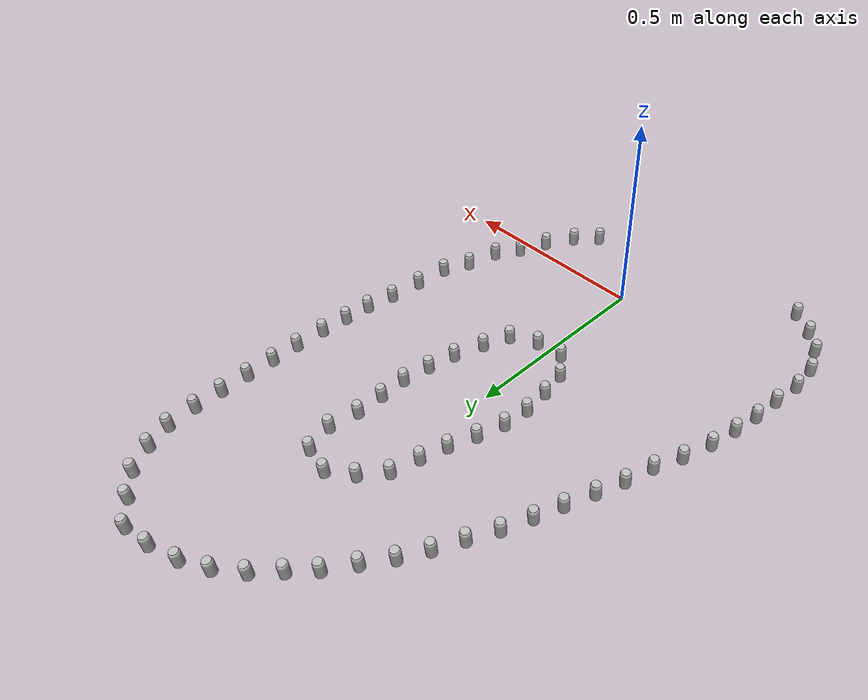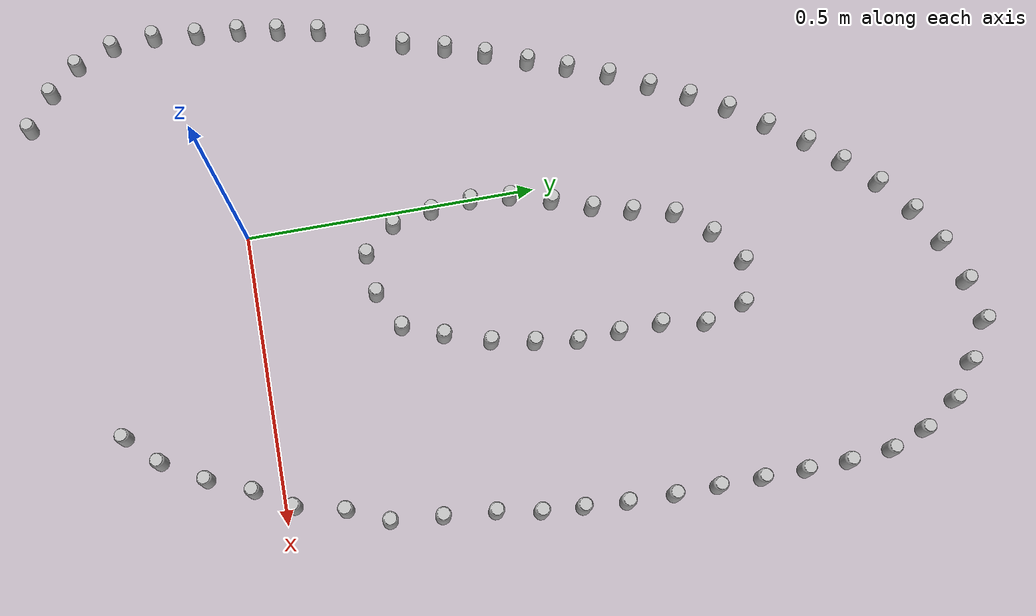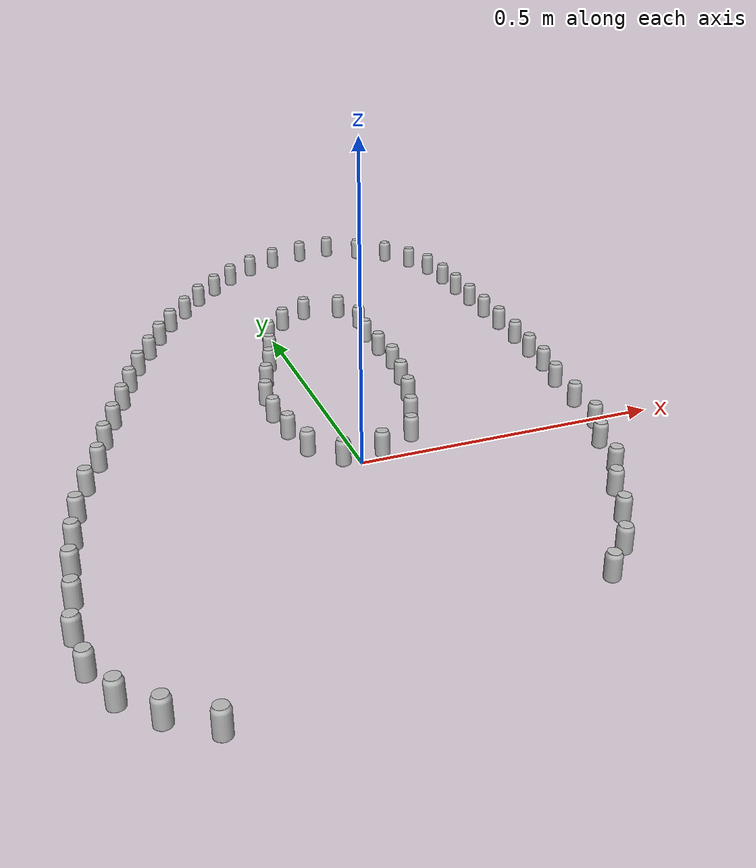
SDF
<sdf version="1.4">
 <world name="default">
  <light name="sun" type="directional">
   <pose>0 0 10 0 -0 0</pose>
   <diffuse>0.8 0.8 0.8 1</diffuse>
   <specular>0.2 0.2 0.2 1</specular>
   <attenuation>
    <range>1000</range>
    <constant>0.9</constant>
    <linear>0.01</linear>
    <quadratic>0.001</quadratic>
   </attenuation>
   <direction>-0.5 0.1 -0.9</direction>
  </light>
  <model name="ground_plane">
   <static>1</static>
   <link name="link">
    <collision name="collision">
     <geometry><plane><normal>0 0 1</normal><size>100 100</size></plane></geometry>
     <surface><friction><ode><mu>100</mu><mu2>50</mu2></ode></friction></surface>
    </collision>
    <visual name="visual">
     <cast_shadows>0</cast_shadows>
     <geometry><plane><normal>0 0 1</normal><size>100 100</size></plane></geometry>
     <material>
      <script><uri>file://media/materials/scripts/gazebo.material</uri><name>Gazebo/Grey</name></script>
     </material>
    </visual>
    <velocity_decay><linear>0</linear><angular>0</angular></velocity_decay>
   </link>
  </model>
  <physics type="ode">
   <max_step_size>0.001</max_step_size>
   <real_time_factor>1</real_time_factor>
   <real_time_update_rate>1000</real_time_update_rate>
   <gravity>0 0 -9.8</gravity>
  </physics>
  <scene><ambient>0.4 0.4 0.4 1</ambient><background>0.7 0.7 0.7 1</background><shadows>1</shadows></scene>
  <spherical_coordinates>
   <surface_model>EARTH_WGS84</surface_model>
   <latitude_deg>0</latitude_deg>
   <longitude_deg>0</longitude_deg>
   <elevation>0</elevation>
   <heading_deg>0</heading_deg>
  </spherical_coordinates>
  <model name="coke_can">
   <static>1</static>
   <link name="link">
    <inertial>
     <pose>-0.01 -0.012 0.15 0 -0 0</pose>
     <mass>0.39</mass>
     <inertia><ixx>0.00058</ixx><ixy>0</ixy><ixz>0</ixz><iyy>0.00058</iyy><iyz>0</iyz><izz>0.00019</izz></inertia>
    </inertial>
    <collision name="collision">
     <pose>0 0 -0.183 0 -0 0</pose>
     <geometry>
      <mesh><uri>model://coke_can/meshes/coke_can.dae</uri><scale>0.398 0.398 0.398</scale></mesh>
     </geometry>
     <surface>
      <friction><ode><mu>1</mu><mu2>1</mu2></ode></friction>
      <contact><ode><kp>1e+07</kp><kd>1</kd><min_depth>0.001</min_depth><max_vel>0.1</max_vel></ode></contact>
     </surface>
    </collision>
    <visual name="visual">
     <pose>0 0 -0.183 0 -0 0</pose>
     <geometry>
      <mesh><uri>model://coke_can/meshes/coke_can.dae</uri><scale>0.398 0.398 0.398</scale></mesh>
     </geometry>
    </visual>
    <velocity_decay><linear>0</linear><angular>0</angular></velocity_decay>
   </link>
   <pose>0.38604 -0.135676 0 0 -0 0</pose>
  </model>
  <model name="coke_can_0">
   <static>1</static>
   <link name="link">
    <inertial>
     <pose>-0.01 -0.012 0.15 0 -0 0</pose>
     <mass>0.39</mass>
     <inertia><ixx>0.00058</ixx><ixy>0</ixy><ixz>0</ixz><iyy>0.00058</iyy><iyz>0</iyz><izz>0.00019</izz></inertia>
    </inertial>
    <collision name="collision">
     <pose>0 0 -0.183 0 -0 0</pose>
     <geometry>
      <mesh><uri>model://coke_can/meshes/coke_can.dae</uri><scale>0.398 0.398 0.398</scale></mesh>
     </geometry>
     <surface>
      <friction><ode><mu>1</mu><mu2>1</mu2></ode></friction>
      <contact><ode><kp>1e+07</kp><kd>1</kd><min_depth>0.001</min_depth><max_vel>0.1</max_vel></ode></contact>
     </surface>
    </collision>
    <visual name="visual">
     <pose>0 0 -0.183 0 -0 0</pose>
     <geometry>
      <mesh><uri>model://coke_can/meshes/coke_can.dae</uri><scale>0.398 0.398 0.398</scale></mesh>
     </geometry>
    </visual>
    <velocity_decay><linear>0</linear><angular>0</angular></velocity_decay>
   </link>
   <pose>0.418667 -0.059022 0 0 -0 0</pose>
  </model>
  <model name="coke_can_2">
   <static>1</static>
   <link name="link">
    <inertial>
     <pose>-0.01 -0.012 0.15 0 -0 0</pose>
     <mass>0.39</mass>
     <inertia><ixx>0.00058</ixx><ixy>0</ixy><ixz>0</ixz><iyy>0.00058</iyy><iyz>0</iyz><izz>0.00019</izz></inertia>
    </inertial>
    <collision name="collision">
     <pose>0 0 -0.183 0 -0 0</pose>
     <geometry>
      <mesh><uri>model://coke_can/meshes/coke_can.dae</uri><scale>0.398 0.398 0.398</scale></mesh>
     </geometry>
     <surface>
      <friction><ode><mu>1</mu><mu2>1</mu2></ode></friction>
      <contact><ode><kp>1e+07</kp><kd>1</kd><min_depth>0.001</min_depth><max_vel>0.1</max_vel></ode></contact>
     </surface>
    </collision>
    <visual name="visual">
     <pose>0 0 -0.183 0 -0 0</pose>
     <geometry>
      <mesh><uri>model://coke_can/meshes/coke_can.dae</uri><scale>0.398 0.398 0.398</scale></mesh>
     </geometry>
    </visual>
    <velocity_decay><linear>0</linear><angular>0</angular></velocity_decay>
   </link>
   <pose>0.288769 -0.265685 0 0 -0 0</pose>
  </model>
  <model name="coke_can_3">
   <static>1</static>
   <link name="link">
    <inertial>
     <pose>-0.01 -0.012 0.15 0 -0 0</pose>
     <mass>0.39</mass>
     <inertia><ixx>0.00058</ixx><ixy>0</ixy><ixz>0</ixz><iyy>0.00058</iyy><iyz>0</iyz><izz>0.00019</izz></inertia>
    </inertial>
    <collision name="collision">
     <pose>0 0 -0.183 0 -0 0</pose>
     <geometry>
      <mesh><uri>model://coke_can/meshes/coke_can.dae</uri><scale>0.398 0.398 0.398</scale></mesh>
     </geometry>
     <surface>
      <friction><ode><mu>1</mu><mu2>1</mu2></ode></friction>
      <contact><ode><kp>1e+07</kp><kd>1</kd><min_depth>0.001</min_depth><max_vel>0.1</max_vel></ode></contact>
     </surface>
    </collision>
    <visual name="visual">
     <pose>0 0 -0.183 0 -0 0</pose>
     <geometry>
      <mesh><uri>model://coke_can/meshes/coke_can.dae</uri><scale>0.398 0.398 0.398</scale></mesh>
     </geometry>
    </visual>
    <velocity_decay><linear>0</linear><angular>0</angular></velocity_decay>
   </link>
   <pose>0.479275 0.091399 0 0 -0 0</pose>
  </model>
  <model name="coke_can_4">
   <static>1</static>
   <link name="link">
    <inertial>
     <pose>-0.01 -0.012 0.15 0 -0 0</pose>
     <mass>0.39</mass>
     <inertia><ixx>0.00058</ixx><ixy>0</ixy><ixz>0</ixz><iyy>0.00058</iyy><iyz>0</iyz><izz>0.00019</izz></inertia>
    </inertial>
    <collision name="collision">
     <pose>0 0 -0.183 0 -0 0</pose>
     <geometry>
      <mesh><uri>model://coke_can/meshes/coke_can.dae</uri><scale>0.398 0.398 0.398</scale></mesh>
     </geometry>
     <surface>
      <friction><ode><mu>1</mu><mu2>1</mu2></ode></friction>
      <contact><ode><kp>1e+07</kp><kd>1</kd><min_depth>0.001</min_depth><max_vel>0.1</max_vel></ode></contact>
     </surface>
    </collision>
    <visual name="visual">
     <pose>0 0 -0.183 0 -0 0</pose>
     <geometry>
      <mesh><uri>model://coke_can/meshes/coke_can.dae</uri><scale>0.398 0.398 0.398</scale></mesh>
     </geometry>
    </visual>
    <velocity_decay><linear>0</linear><angular>0</angular></velocity_decay>
   </link>
   <pose>0.457915 0.005194 0 0 -0 0</pose>
  </model>
  <model name="coke_can_5">
   <static>1</static>
   <link name="link">
    <inertial>
     <pose>-0.01 -0.012 0.15 0 -0 0</pose>
     <mass>0.39</mass>
     <inertia><ixx>0.00058</ixx><ixy>0</ixy><ixz>0</ixz><iyy>0.00058</iyy><iyz>0</iyz><izz>0.00019</izz></inertia>
    </inertial>
    <collision name="collision">
     <pose>0 0 -0.183 0 -0 0</pose>
     <geometry>
      <mesh><uri>model://coke_can/meshes/coke_can.dae</uri><scale>0.398 0.398 0.398</scale></mesh>
     </geometry>
     <surface>
      <friction><ode><mu>1</mu><mu2>1</mu2></ode></friction>
      <contact><ode><kp>1e+07</kp><kd>1</kd><min_depth>0.001</min_depth><max_vel>0.1</max_vel></ode></contact>
     </surface>
    </collision>
    <visual name="visual">
     <pose>0 0 -0.183 0 -0 0</pose>
     <geometry>
      <mesh><uri>model://coke_can/meshes/coke_can.dae</uri><scale>0.398 0.398 0.398</scale></mesh>
     </geometry>
    </visual>
    <velocity_decay><linear>0</linear><angular>0</angular></velocity_decay>
   </link>
   <pose>0.341948 -0.210761 0 0 -0 0</pose>
  </model>
  <model name="coke_can_6">
   <static>1</static>
   <link name="link">
    <inertial>
     <mass>0.39</mass>
     <inertia><ixx>0.00058</ixx><ixy>0</ixy><ixz>0</ixz><iyy>0.00058</iyy><iyz>0</iyz><izz>0.00019</izz></inertia>
    </inertial>
    <collision name="collision">
     <pose>0 0 -0.183 0 -0 0</pose>
     <geometry>
      <mesh><uri>model://coke_can/meshes/coke_can.dae</uri><scale>0.398 0.398 0.398</scale></mesh>
     </geometry>
     <surface>
      <friction><ode><mu>1</mu><mu2>1</mu2></ode></friction>
      <contact><ode><kp>1e+07</kp><kd>1</kd><min_depth>0.001</min_depth><max_vel>0.1</max_vel></ode></contact>
     </surface>
    </collision>
    <visual name="visual">
     <pose>0 0 -0.183 0 -0 0</pose>
     <geometry>
      <mesh><uri>model://coke_can/meshes/coke_can.dae</uri><scale>0.398 0.398 0.398</scale></mesh>
     </geometry>
    </visual>
    <velocity_decay><linear>0</linear><angular>0</angular></velocity_decay>
   </link>
   <pose>0.511163 0.167151 -0.001657 -0.05647 0.004812 0.001626</pose>
   <static>0</static>
  </model>
  <model name="coke_can_7">
   <static>1</static>
   <link name="link">
    <inertial>
     <mass>0.39</mass>
     <inertia><ixx>0.00058</ixx><ixy>0</ixy><ixz>0</ixz><iyy>0.00058</iyy><iyz>0</iyz><izz>0.00019</izz></inertia>
    </inertial>
    <collision name="collision">
     <pose>0 0 -0.183 0 -0 0</pose>
     <geometry>
      <mesh><uri>model://coke_can/meshes/coke_can.dae</uri><scale>0.398 0.398 0.398</scale></mesh>
     </geometry>
     <surface>
      <friction><ode><mu>1</mu><mu2>1</mu2></ode></friction>
      <contact><ode><kp>1e+07</kp><kd>1</kd><min_depth>0.001</min_depth><max_vel>0.1</max_vel></ode></contact>
     </surface>
    </collision>
    <visual name="visual">
     <pose>0 0 -0.183 0 -0 0</pose>
     <geometry>
      <mesh><uri>model://coke_can/meshes/coke_can.dae</uri><scale>0.398 0.398 0.398</scale></mesh>
     </geometry>
    </visual>
    <velocity_decay><linear>0</linear><angular>0</angular></velocity_decay>
   </link>
   <pose>0.519485 0.256787 -0.001657 -0.05647 0.004812 0.001626</pose>
   <static>0</static>
  </model>
  <model name="coke_can_8">
   <static>1</static>
   <link name="link">
    <inertial>
     <mass>0.39</mass>
     <inertia><ixx>0.00058</ixx><ixy>0</ixy><ixz>0</ixz><iyy>0.00058</iyy><iyz>0</iyz><izz>0.00019</izz></inertia>
    </inertial>
    <collision name="collision">
     <pose>0 0 -0.183 0 -0 0</pose>
     <geometry>
      <mesh><uri>model://coke_can/meshes/coke_can.dae</uri><scale>0.398 0.398 0.398</scale></mesh>
     </geometry>
     <surface>
      <friction><ode><mu>1</mu><mu2>1</mu2></ode></friction>
      <contact><ode><kp>1e+07</kp><kd>1</kd><min_depth>0.001</min_depth><max_vel>0.1</max_vel></ode></contact>
     </surface>
    </collision>
    <visual name="visual">
     <pose>0 0 -0.183 0 -0 0</pose>
     <geometry>
      <mesh><uri>model://coke_can/meshes/coke_can.dae</uri><scale>0.398 0.398 0.398</scale></mesh>
     </geometry>
    </visual>
    <velocity_decay><linear>0</linear><angular>0</angular></velocity_decay>
   </link>
   <pose>0.52765 0.34668 -0.001657 -0.05647 0.004812 0.001626</pose>
   <static>0</static>
  </model>
  <model name="coke_can_9">
   <static>1</static>
   <link name="link">
    <inertial>
     <mass>0.39</mass>
     <inertia><ixx>0.00058</ixx><ixy>0</ixy><ixz>0</ixz><iyy>0.00058</iyy><iyz>0</iyz><izz>0.00019</izz></inertia>
    </inertial>
    <collision name="collision">
     <pose>0 0 -0.183 0 -0 0</pose>
     <geometry>
      <mesh><uri>model://coke_can/meshes/coke_can.dae</uri><scale>0.398 0.398 0.398</scale></mesh>
     </geometry>
     <surface>
      <friction><ode><mu>1</mu><mu2>1</mu2></ode></friction>
      <contact><ode><kp>1e+07</kp><kd>1</kd><min_depth>0.001</min_depth><max_vel>0.1</max_vel></ode></contact>
     </surface>
    </collision>
    <visual name="visual">
     <pose>0 0 -0.183 0 -0 0</pose>
     <geometry>
      <mesh><uri>model://coke_can/meshes/coke_can.dae</uri><scale>0.398 0.398 0.398</scale></mesh>
     </geometry>
    </visual>
    <velocity_decay><linear>0</linear><angular>0</angular></velocity_decay>
   </link>
   <pose>0.541619 0.42249 -0.001657 -0.05647 0.004812 0.001626</pose>
   <static>0</static>
  </model>
  <model name="coke_can_10">
   <static>1</static>
   <link name="link">
    <inertial>
     <mass>0.39</mass>
     <inertia><ixx>0.00058</ixx><ixy>0</ixy><ixz>0</ixz><iyy>0.00058</iyy><iyz>0</iyz><izz>0.00019</izz></inertia>
    </inertial>
    <collision name="collision">
     <pose>0 0 -0.183 0 -0 0</pose>
     <geometry>
      <mesh><uri>model://coke_can/meshes/coke_can.dae</uri><scale>0.398 0.398 0.398</scale></mesh>
     </geometry>
     <surface>
      <friction><ode><mu>1</mu><mu2>1</mu2></ode></friction>
      <contact><ode><kp>1e+07</kp><kd>1</kd><min_depth>0.001</min_depth><max_vel>0.1</max_vel></ode></contact>
     </surface>
    </collision>
    <visual name="visual">
     <pose>0 0 -0.183 0 -0 0</pose>
     <geometry>
      <mesh><uri>model://coke_can/meshes/coke_can.dae</uri><scale>0.398 0.398 0.398</scale></mesh>
     </geometry>
    </visual>
    <velocity_decay><linear>0</linear><angular>0</angular></velocity_decay>
   </link>
   <pose>0.546737 0.494536 -0.001657 -0.05647 0.004812 0.001626</pose>
   <static>0</static>
  </model>
  <model name="coke_can_11">
   <static>1</static>
   <link name="link">
    <inertial>
     <mass>0.39</mass>
     <inertia><ixx>0.00058</ixx><ixy>0</ixy><ixz>0</ixz><iyy>0.00058</iyy><iyz>0</iyz><izz>0.00019</izz></inertia>
    </inertial>
    <collision name="collision">
     <pose>0 0 -0.183 0 -0 0</pose>
     <geometry>
      <mesh><uri>model://coke_can/meshes/coke_can.dae</uri><scale>0.398 0.398 0.398</scale></mesh>
     </geometry>
     <surface>
      <friction><ode><mu>1</mu><mu2>1</mu2></ode></friction>
      <contact><ode><kp>1e+07</kp><kd>1</kd><min_depth>0.001</min_depth><max_vel>0.1</max_vel></ode></contact>
     </surface>
    </collision>
    <visual name="visual">
     <pose>0 0 -0.183 0 -0 0</pose>
     <geometry>
      <mesh><uri>model://coke_can/meshes/coke_can.dae</uri><scale>0.398 0.398 0.398</scale></mesh>
     </geometry>
    </visual>
    <velocity_decay><linear>0</linear><angular>0</angular></velocity_decay>
   </link>
   <pose>0.551856 0.569792 -0.001657 -0.05647 0.004812 0.001626</pose>
   <static>0</static>
  </model>
  <model name="coke_can_12">
   <static>1</static>
   <link name="link">
    <inertial>
     <mass>0.39</mass>
     <inertia><ixx>0.00058</ixx><ixy>0</ixy><ixz>0</ixz><iyy>0.00058</iyy><iyz>0</iyz><izz>0.00019</izz></inertia>
    </inertial>
    <collision name="collision">
     <pose>0 0 -0.183 0 -0 0</pose>
     <geometry>
      <mesh><uri>model://coke_can/meshes/coke_can.dae</uri><scale>0.398 0.398 0.398</scale></mesh>
     </geometry>
     <surface>
      <friction><ode><mu>1</mu><mu2>1</mu2></ode></friction>
      <contact><ode><kp>1e+07</kp><kd>1</kd><min_depth>0.001</min_depth><max_vel>0.1</max_vel></ode></contact>
     </surface>
    </collision>
    <visual name="visual">
     <pose>0 0 -0.183 0 -0 0</pose>
     <geometry>
      <mesh><uri>model://coke_can/meshes/coke_can.dae</uri><scale>0.398 0.398 0.398</scale></mesh>
     </geometry>
    </visual>
    <velocity_decay><linear>0</linear><angular>0</angular></velocity_decay>
   </link>
   <pose>0.553953 0.651431 -0.001657 -0.05647 0.004812 0.001626</pose>
   <static>0</static>
  </model>
  <model name="coke_can_13">
   <static>1</static>
   <link name="link">
    <inertial>
     <mass>0.39</mass>
     <inertia><ixx>0.00058</ixx><ixy>0</ixy><ixz>0</ixz><iyy>0.00058</iyy><iyz>0</iyz><izz>0.00019</izz></inertia>
    </inertial>
    <collision name="collision">
     <pose>0 0 -0.183 0 -0 0</pose>
     <geometry>
      <mesh><uri>model://coke_can/meshes/coke_can.dae</uri><scale>0.398 0.398 0.398</scale></mesh>
     </geometry>
     <surface>
      <friction><ode><mu>1</mu><mu2>1</mu2></ode></friction>
      <contact><ode><kp>1e+07</kp><kd>1</kd><min_depth>0.001</min_depth><max_vel>0.1</max_vel></ode></contact>
     </surface>
    </collision>
    <visual name="visual">
     <pose>0 0 -0.183 0 -0 0</pose>
     <geometry>
      <mesh><uri>model://coke_can/meshes/coke_can.dae</uri><scale>0.398 0.398 0.398</scale></mesh>
     </geometry>
    </visual>
    <velocity_decay><linear>0</linear><angular>0</angular></velocity_decay>
   </link>
   <pose>0.55358 0.727718 -0.001657 -0.05647 0.004812 0.001626</pose>
   <static>0</static>
  </model>
  <model name="coke_can_14">
   <static>1</static>
   <link name="link">
    <inertial>
     <mass>0.39</mass>
     <inertia><ixx>0.00058</ixx><ixy>0</ixy><ixz>0</ixz><iyy>0.00058</iyy><iyz>0</iyz><izz>0.00019</izz></inertia>
    </inertial>
    <collision name="collision">
     <pose>0 0 -0.183 0 -0 0</pose>
     <geometry>
      <mesh><uri>model://coke_can/meshes/coke_can.dae</uri><scale>0.398 0.398 0.398</scale></mesh>
     </geometry>
     <surface>
      <friction><ode><mu>1</mu><mu2>1</mu2></ode></friction>
      <contact><ode><kp>1e+07</kp><kd>1</kd><min_depth>0.001</min_depth><max_vel>0.1</max_vel></ode></contact>
     </surface>
    </collision>
    <visual name="visual">
     <pose>0 0 -0.183 0 -0 0</pose>
     <geometry>
      <mesh><uri>model://coke_can/meshes/coke_can.dae</uri><scale>0.398 0.398 0.398</scale></mesh>
     </geometry>
    </visual>
    <velocity_decay><linear>0</linear><angular>0</angular></velocity_decay>
   </link>
   <pose>0.553579 0.804939 -0.001657 -0.05647 0.004812 0.001626</pose>
   <static>0</static>
  </model>
  <model name="coke_can_15">
   <static>1</static>
   <link name="link">
    <inertial>
     <mass>0.39</mass>
     <inertia><ixx>0.00058</ixx><ixy>0</ixy><ixz>0</ixz><iyy>0.00058</iyy><iyz>0</iyz><izz>0.00019</izz></inertia>
    </inertial>
    <collision name="collision">
     <pose>0 0 -0.183 0 -0 0</pose>
     <geometry>
      <mesh><uri>model://coke_can/meshes/coke_can.dae</uri><scale>0.398 0.398 0.398</scale></mesh>
     </geometry>
     <surface>
      <friction><ode><mu>1</mu><mu2>1</mu2></ode></friction>
      <contact><ode><kp>1e+07</kp><kd>1</kd><min_depth>0.001</min_depth><max_vel>0.1</max_vel></ode></contact>
     </surface>
    </collision>
    <visual name="visual">
     <pose>0 0 -0.183 0 -0 0</pose>
     <geometry>
      <mesh><uri>model://coke_can/meshes/coke_can.dae</uri><scale>0.398 0.398 0.398</scale></mesh>
     </geometry>
    </visual>
    <velocity_decay><linear>0</linear><angular>0</angular></velocity_decay>
   </link>
   <pose>0.552971 0.881645 -0.001657 -0.05647 0.004812 0.001626</pose>
   <static>0</static>
  </model>
  <model name="coke_can_16">
   <static>1</static>
   <link name="link">
    <inertial>
     <mass>0.39</mass>
     <inertia><ixx>0.00058</ixx><ixy>0</ixy><ixz>0</ixz><iyy>0.00058</iyy><iyz>0</iyz><izz>0.00019</izz></inertia>
    </inertial>
    <collision name="collision">
     <pose>0 0 -0.183 0 -0 0</pose>
     <geometry>
      <mesh><uri>model://coke_can/meshes/coke_can.dae</uri><scale>0.398 0.398 0.398</scale></mesh>
     </geometry>
     <surface>
      <friction><ode><mu>1</mu><mu2>1</mu2></ode></friction>
      <contact><ode><kp>1e+07</kp><kd>1</kd><min_depth>0.001</min_depth><max_vel>0.1</max_vel></ode></contact>
     </surface>
    </collision>
    <visual name="visual">
     <pose>0 0 -0.183 0 -0 0</pose>
     <geometry>
      <mesh><uri>model://coke_can/meshes/coke_can.dae</uri><scale>0.398 0.398 0.398</scale></mesh>
     </geometry>
    </visual>
    <velocity_decay><linear>0</linear><angular>0</angular></velocity_decay>
   </link>
   <pose>0.551859 0.957143 -0.001657 -0.05647 0.004812 0.001626</pose>
   <static>0</static>
  </model>
  <model name="coke_can_17">
   <static>1</static>
   <link name="link">
    <inertial>
     <mass>0.39</mass>
     <inertia><ixx>0.00058</ixx><ixy>0</ixy><ixz>0</ixz><iyy>0.00058</iyy><iyz>0</iyz><izz>0.00019</izz></inertia>
    </inertial>
    <collision name="collision">
     <pose>0 0 -0.183 0 -0 0</pose>
     <geometry>
      <mesh><uri>model://coke_can/meshes/coke_can.dae</uri><scale>0.398 0.398 0.398</scale></mesh>
     </geometry>
     <surface>
      <friction><ode><mu>1</mu><mu2>1</mu2></ode></friction>
      <contact><ode><kp>1e+07</kp><kd>1</kd><min_depth>0.001</min_depth><max_vel>0.1</max_vel></ode></contact>
     </surface>
    </collision>
    <visual name="visual">
     <pose>0 0 -0.183 0 -0 0</pose>
     <geometry>
      <mesh><uri>model://coke_can/meshes/coke_can.dae</uri><scale>0.398 0.398 0.398</scale></mesh>
     </geometry>
    </visual>
    <velocity_decay><linear>0</linear><angular>0</angular></velocity_decay>
   </link>
   <pose>0.544914 1.03438 -0.001657 -0.05647 0.004812 0.001626</pose>
   <static>0</static>
  </model>
  <model name="coke_can_18">
   <static>1</static>
   <link name="link">
    <inertial>
     <mass>0.39</mass>
     <inertia><ixx>0.00058</ixx><ixy>0</ixy><ixz>0</ixz><iyy>0.00058</iyy><iyz>0</iyz><izz>0.00019</izz></inertia>
    </inertial>
    <collision name="collision">
     <pose>0 0 -0.183 0 -0 0</pose>
     <geometry>
      <mesh><uri>model://coke_can/meshes/coke_can.dae</uri><scale>0.398 0.398 0.398</scale></mesh>
     </geometry>
     <surface>
      <friction><ode><mu>1</mu><mu2>1</mu2></ode></friction>
      <contact><ode><kp>1e+07</kp><kd>1</kd><min_depth>0.001</min_depth><max_vel>0.1</max_vel></ode></contact>
     </surface>
    </collision>
    <visual name="visual">
     <pose>0 0 -0.183 0 -0 0</pose>
     <geometry>
      <mesh><uri>model://coke_can/meshes/coke_can.dae</uri><scale>0.398 0.398 0.398</scale></mesh>
     </geometry>
    </visual>
    <velocity_decay><linear>0</linear><angular>0</angular></velocity_decay>
   </link>
   <pose>0.52107 1.09986 -0.001657 -0.05647 0.004812 0.001626</pose>
   <static>0</static>
  </model>
  <model name="coke_can_19">
   <static>1</static>
   <link name="link">
    <inertial>
     <mass>0.39</mass>
     <inertia><ixx>0.00058</ixx><ixy>0</ixy><ixz>0</ixz><iyy>0.00058</iyy><iyz>0</iyz><izz>0.00019</izz></inertia>
    </inertial>
    <collision name="collision">
     <pose>0 0 -0.183 0 -0 0</pose>
     <geometry>
      <mesh><uri>model://coke_can/meshes/coke_can.dae</uri><scale>0.398 0.398 0.398</scale></mesh>
     </geometry>
     <surface>
      <friction><ode><mu>1</mu><mu2>1</mu2></ode></friction>
      <contact><ode><kp>1e+07</kp><kd>1</kd><min_depth>0.001</min_depth><max_vel>0.1</max_vel></ode></contact>
     </surface>
    </collision>
    <visual name="visual">
     <pose>0 0 -0.183 0 -0 0</pose>
     <geometry>
      <mesh><uri>model://coke_can/meshes/coke_can.dae</uri><scale>0.398 0.398 0.398</scale></mesh>
     </geometry>
    </visual>
    <velocity_decay><linear>0</linear><angular>0</angular></velocity_decay>
   </link>
   <pose>0.480327 1.16398 -0.001657 -0.05647 0.004812 0.001626</pose>
   <static>0</static>
  </model>
  <model name="coke_can_20">
   <static>1</static>
   <link name="link">
    <inertial>
     <mass>0.39</mass>
     <inertia><ixx>0.00058</ixx><ixy>0</ixy><ixz>0</ixz><iyy>0.00058</iyy><iyz>0</iyz><izz>0.00019</izz></inertia>
    </inertial>
    <collision name="collision">
     <pose>0 0 -0.183 0 -0 0</pose>
     <geometry>
      <mesh><uri>model://coke_can/meshes/coke_can.dae</uri><scale>0.398 0.398 0.398</scale></mesh>
     </geometry>
     <surface>
      <friction><ode><mu>1</mu><mu2>1</mu2></ode></friction>
      <contact><ode><kp>1e+07</kp><kd>1</kd><min_depth>0.001</min_depth><max_vel>0.1</max_vel></ode></contact>
     </surface>
    </collision>
    <visual name="visual">
     <pose>0 0 -0.183 0 -0 0</pose>
     <geometry>
      <mesh><uri>model://coke_can/meshes/coke_can.dae</uri><scale>0.398 0.398 0.398</scale></mesh>
     </geometry>
    </visual>
    <velocity_decay><linear>0</linear><angular>0</angular></velocity_decay>
   </link>
   <pose>0.419583 1.20952 -0.001657 -0.05647 0.004812 0.001626</pose>
   <static>0</static>
  </model>
  <model name="coke_can_21">
   <static>1</static>
   <link name="link">
    <inertial>
     <mass>0.39</mass>
     <inertia><ixx>0.00058</ixx><ixy>0</ixy><ixz>0</ixz><iyy>0.00058</iyy><iyz>0</iyz><izz>0.00019</izz></inertia>
    </inertial>
    <collision name="collision">
     <pose>0 0 -0.183 0 -0 0</pose>
     <geometry>
      <mesh><uri>model://coke_can/meshes/coke_can.dae</uri><scale>0.398 0.398 0.398</scale></mesh>
     </geometry>
     <surface>
      <friction><ode><mu>1</mu><mu2>1</mu2></ode></friction>
      <contact><ode><kp>1e+07</kp><kd>1</kd><min_depth>0.001</min_depth><max_vel>0.1</max_vel></ode></contact>
     </surface>
    </collision>
    <visual name="visual">
     <pose>0 0 -0.183 0 -0 0</pose>
     <geometry>
      <mesh><uri>model://coke_can/meshes/coke_can.dae</uri><scale>0.398 0.398 0.398</scale></mesh>
     </geometry>
    </visual>
    <velocity_decay><linear>0</linear><angular>0</angular></velocity_decay>
   </link>
   <pose>0.352083 1.25266 -0.001657 -0.05647 0.004812 0.001626</pose>
   <static>0</static>
  </model>
  <model name="coke_can_22">
   <static>1</static>
   <link name="link">
    <inertial>
     <mass>0.39</mass>
     <inertia><ixx>0.00058</ixx><ixy>0</ixy><ixz>0</ixz><iyy>0.00058</iyy><iyz>0</iyz><izz>0.00019</izz></inertia>
    </inertial>
    <collision name="collision">
     <pose>0 0 -0.183 0 -0 0</pose>
     <geometry>
      <mesh><uri>model://coke_can/meshes/coke_can.dae</uri><scale>0.398 0.398 0.398</scale></mesh>
     </geometry>
     <surface>
      <friction><ode><mu>1</mu><mu2>1</mu2></ode></friction>
      <contact><ode><kp>1e+07</kp><kd>1</kd><min_depth>0.001</min_depth><max_vel>0.1</max_vel></ode></contact>
     </surface>
    </collision>
    <visual name="visual">
     <pose>0 0 -0.183 0 -0 0</pose>
     <geometry>
      <mesh><uri>model://coke_can/meshes/coke_can.dae</uri><scale>0.398 0.398 0.398</scale></mesh>
     </geometry>
    </visual>
    <velocity_decay><linear>0</linear><angular>0</angular></velocity_decay>
   </link>
   <pose>0.275952 1.24191 -0.001657 -0.05647 0.004812 0.001626</pose>
   <static>0</static>
  </model>
  <model name="coke_can_23">
   <static>1</static>
   <link name="link">
    <inertial>
     <mass>0.39</mass>
     <inertia><ixx>0.00058</ixx><ixy>0</ixy><ixz>0</ixz><iyy>0.00058</iyy><iyz>0</iyz><izz>0.00019</izz></inertia>
    </inertial>
    <collision name="collision">
     <pose>0 0 -0.183 0 -0 0</pose>
     <geometry>
      <mesh><uri>model://coke_can/meshes/coke_can.dae</uri><scale>0.398 0.398 0.398</scale></mesh>
     </geometry>
     <surface>
      <friction><ode><mu>1</mu><mu2>1</mu2></ode></friction>
      <contact><ode><kp>1e+07</kp><kd>1</kd><min_depth>0.001</min_depth><max_vel>0.1</max_vel></ode></contact>
     </surface>
    </collision>
    <visual name="visual">
     <pose>0 0 -0.183 0 -0 0</pose>
     <geometry>
      <mesh><uri>model://coke_can/meshes/coke_can.dae</uri><scale>0.398 0.398 0.398</scale></mesh>
     </geometry>
    </visual>
    <velocity_decay><linear>0</linear><angular>0</angular></velocity_decay>
   </link>
   <pose>0.197094 1.21748 -0.001657 -0.05647 0.004812 0.001626</pose>
   <static>0</static>
  </model>
  <model name="coke_can_24">
   <static>1</static>
   <link name="link">
    <inertial>
     <mass>0.39</mass>
     <inertia><ixx>0.00058</ixx><ixy>0</ixy><ixz>0</ixz><iyy>0.00058</iyy><iyz>0</iyz><izz>0.00019</izz></inertia>
    </inertial>
    <collision name="collision">
     <pose>0 0 -0.183 0 -0 0</pose>
     <geometry>
      <mesh><uri>model://coke_can/meshes/coke_can.dae</uri><scale>0.398 0.398 0.398</scale></mesh>
     </geometry>
     <surface>
      <friction><ode><mu>1</mu><mu2>1</mu2></ode></friction>
      <contact><ode><kp>1e+07</kp><kd>1</kd><min_depth>0.001</min_depth><max_vel>0.1</max_vel></ode></contact>
     </surface>
    </collision>
    <visual name="visual">
     <pose>0 0 -0.183 0 -0 0</pose>
     <geometry>
      <mesh><uri>model://coke_can/meshes/coke_can.dae</uri><scale>0.398 0.398 0.398</scale></mesh>
     </geometry>
    </visual>
    <velocity_decay><linear>0</linear><angular>0</angular></velocity_decay>
   </link>
   <pose>0.129825 1.18197 -0.001657 -0.05647 0.004812 0.001626</pose>
   <static>0</static>
  </model>
  <model name="coke_can_25">
   <static>1</static>
   <link name="link">
    <inertial>
     <mass>0.39</mass>
     <inertia><ixx>0.00058</ixx><ixy>0</ixy><ixz>0</ixz><iyy>0.00058</iyy><iyz>0</iyz><izz>0.00019</izz></inertia>
    </inertial>
    <collision name="collision">
     <pose>0 0 -0.183 0 -0 0</pose>
     <geometry>
      <mesh><uri>model://coke_can/meshes/coke_can.dae</uri><scale>0.398 0.398 0.398</scale></mesh>
     </geometry>
     <surface>
      <friction><ode><mu>1</mu><mu2>1</mu2></ode></friction>
      <contact><ode><kp>1e+07</kp><kd>1</kd><min_depth>0.001</min_depth><max_vel>0.1</max_vel></ode></contact>
     </surface>
    </collision>
    <visual name="visual">
     <pose>0 0 -0.183 0 -0 0</pose>
     <geometry>
      <mesh><uri>model://coke_can/meshes/coke_can.dae</uri><scale>0.398 0.398 0.398</scale></mesh>
     </geometry>
    </visual>
    <velocity_decay><linear>0</linear><angular>0</angular></velocity_decay>
   </link>
   <pose>0.068113 1.13449 -0.001657 -0.05647 0.004812 0.001626</pose>
   <static>0</static>
  </model>
  <model name="coke_can_26">
   <static>1</static>
   <link name="link">
    <inertial>
     <mass>0.39</mass>
     <inertia><ixx>0.00058</ixx><ixy>0</ixy><ixz>0</ixz><iyy>0.00058</iyy><iyz>0</iyz><izz>0.00019</izz></inertia>
    </inertial>
    <collision name="collision">
     <pose>0 0 -0.183 0 -0 0</pose>
     <geometry>
      <mesh><uri>model://coke_can/meshes/coke_can.dae</uri><scale>0.398 0.398 0.398</scale></mesh>
     </geometry>
     <surface>
      <friction><ode><mu>1</mu><mu2>1</mu2></ode></friction>
      <contact><ode><kp>1e+07</kp><kd>1</kd><min_depth>0.001</min_depth><max_vel>0.1</max_vel></ode></contact>
     </surface>
    </collision>
    <visual name="visual">
     <pose>0 0 -0.183 0 -0 0</pose>
     <geometry>
      <mesh><uri>model://coke_can/meshes/coke_can.dae</uri><scale>0.398 0.398 0.398</scale></mesh>
     </geometry>
    </visual>
    <velocity_decay><linear>0</linear><angular>0</angular></velocity_decay>
   </link>
   <pose>0.01566 1.07888 -0.001657 -0.05647 0.004812 0.001626</pose>
   <static>0</static>
  </model>
  <model name="coke_can_27">
   <static>1</static>
   <link name="link">
    <inertial>
     <mass>0.39</mass>
     <inertia><ixx>0.00058</ixx><ixy>0</ixy><ixz>0</ixz><iyy>0.00058</iyy><iyz>0</iyz><izz>0.00019</izz></inertia>
    </inertial>
    <collision name="collision">
     <pose>0 0 -0.183 0 -0 0</pose>
     <geometry>
      <mesh><uri>model://coke_can/meshes/coke_can.dae</uri><scale>0.398 0.398 0.398</scale></mesh>
     </geometry>
     <surface>
      <friction><ode><mu>1</mu><mu2>1</mu2></ode></friction>
      <contact><ode><kp>1e+07</kp><kd>1</kd><min_depth>0.001</min_depth><max_vel>0.1</max_vel></ode></contact>
     </surface>
    </collision>
    <visual name="visual">
     <pose>0 0 -0.183 0 -0 0</pose>
     <geometry>
      <mesh><uri>model://coke_can/meshes/coke_can.dae</uri><scale>0.398 0.398 0.398</scale></mesh>
     </geometry>
    </visual>
    <velocity_decay><linear>0</linear><angular>0</angular></velocity_decay>
   </link>
   <pose>-0.033824 1.02561 -0.001657 -0.05647 0.004812 0.001626</pose>
   <static>0</static>
  </model>
  <model name="coke_can_28">
   <static>1</static>
   <link name="link">
    <inertial>
     <mass>0.39</mass>
     <inertia><ixx>0.00058</ixx><ixy>0</ixy><ixz>0</ixz><iyy>0.00058</iyy><iyz>0</iyz><izz>0.00019</izz></inertia>
    </inertial>
    <collision name="collision">
     <pose>0 0 -0.183 0 -0 0</pose>
     <geometry>
      <mesh><uri>model://coke_can/meshes/coke_can.dae</uri><scale>0.398 0.398 0.398</scale></mesh>
     </geometry>
     <surface>
      <friction><ode><mu>1</mu><mu2>1</mu2></ode></friction>
      <contact><ode><kp>1e+07</kp><kd>1</kd><min_depth>0.001</min_depth><max_vel>0.1</max_vel></ode></contact>
     </surface>
    </collision>
    <visual name="visual">
     <pose>0 0 -0.183 0 -0 0</pose>
     <geometry>
      <mesh><uri>model://coke_can/meshes/coke_can.dae</uri><scale>0.398 0.398 0.398</scale></mesh>
     </geometry>
    </visual>
    <velocity_decay><linear>0</linear><angular>0</angular></velocity_decay>
   </link>
   <pose>-0.079271 0.961086 -0.001657 -0.05647 0.004812 0.001626</pose>
   <static>0</static>
  </model>
  <model name="coke_can_29">
   <static>1</static>
   <link name="link">
    <inertial>
     <mass>0.39</mass>
     <inertia><ixx>0.00058</ixx><ixy>0</ixy><ixz>0</ixz><iyy>0.00058</iyy><iyz>0</iyz><izz>0.00019</izz></inertia>
    </inertial>
    <collision name="collision">
     <pose>0 0 -0.183 0 -0 0</pose>
     <geometry>
      <mesh><uri>model://coke_can/meshes/coke_can.dae</uri><scale>0.398 0.398 0.398</scale></mesh>
     </geometry>
     <surface>
      <friction><ode><mu>1</mu><mu2>1</mu2></ode></friction>
      <contact><ode><kp>1e+07</kp><kd>1</kd><min_depth>0.001</min_depth><max_vel>0.1</max_vel></ode></contact>
     </surface>
    </collision>
    <visual name="visual">
     <pose>0 0 -0.183 0 -0 0</pose>
     <geometry>
      <mesh><uri>model://coke_can/meshes/coke_can.dae</uri><scale>0.398 0.398 0.398</scale></mesh>
     </geometry>
    </visual>
    <velocity_decay><linear>0</linear><angular>0</angular></velocity_decay>
   </link>
   <pose>-0.124004 0.898088 -0.001657 -0.05647 0.004812 0.001626</pose>
   <static>0</static>
  </model>
  <model name="coke_can_30">
   <static>1</static>
   <link name="link">
    <inertial>
     <mass>0.39</mass>
     <inertia><ixx>0.00058</ixx><ixy>0</ixy><ixz>0</ixz><iyy>0.00058</iyy><iyz>0</iyz><izz>0.00019</izz></inertia>
    </inertial>
    <collision name="collision">
     <pose>0 0 -0.183 0 -0 0</pose>
     <geometry>
      <mesh><uri>model://coke_can/meshes/coke_can.dae</uri><scale>0.398 0.398 0.398</scale></mesh>
     </geometry>
     <surface>
      <friction><ode><mu>1</mu><mu2>1</mu2></ode></friction>
      <contact><ode><kp>1e+07</kp><kd>1</kd><min_depth>0.001</min_depth><max_vel>0.1</max_vel></ode></contact>
     </surface>
    </collision>
    <visual name="visual">
     <pose>0 0 -0.183 0 -0 0</pose>
     <geometry>
      <mesh><uri>model://coke_can/meshes/coke_can.dae</uri><scale>0.398 0.398 0.398</scale></mesh>
     </geometry>
    </visual>
    <velocity_decay><linear>0</linear><angular>0</angular></velocity_decay>
   </link>
   <pose>-0.160362 0.833004 -0.001657 -0.05647 0.004812 0.001626</pose>
   <static>0</static>
  </model>
  <model name="coke_can_31">
   <static>1</static>
   <link name="link">
    <inertial>
     <mass>0.39</mass>
     <inertia><ixx>0.00058</ixx><ixy>0</ixy><ixz>0</ixz><iyy>0.00058</iyy><iyz>0</iyz><izz>0.00019</izz></inertia>
    </inertial>
    <collision name="collision">
     <pose>0 0 -0.183 0 -0 0</pose>
     <geometry>
      <mesh><uri>model://coke_can/meshes/coke_can.dae</uri><scale>0.398 0.398 0.398</scale></mesh>
     </geometry>
     <surface>
      <friction><ode><mu>1</mu><mu2>1</mu2></ode></friction>
      <contact><ode><kp>1e+07</kp><kd>1</kd><min_depth>0.001</min_depth><max_vel>0.1</max_vel></ode></contact>
     </surface>
    </collision>
    <visual name="visual">
     <pose>0 0 -0.183 0 -0 0</pose>
     <geometry>
      <mesh><uri>model://coke_can/meshes/coke_can.dae</uri><scale>0.398 0.398 0.398</scale></mesh>
     </geometry>
    </visual>
    <velocity_decay><linear>0</linear><angular>0</angular></velocity_decay>
   </link>
   <pose>-0.194389 0.764948 -0.001657 -0.05647 0.004812 0.001626</pose>
   <static>0</static>
  </model>
  <model name="coke_can_32">
   <static>1</static>
   <link name="link">
    <inertial>
     <mass>0.39</mass>
     <inertia><ixx>0.00058</ixx><ixy>0</ixy><ixz>0</ixz><iyy>0.00058</iyy><iyz>0</iyz><izz>0.00019</izz></inertia>
    </inertial>
    <collision name="collision">
     <pose>0 0 -0.183 0 -0 0</pose>
     <geometry>
      <mesh><uri>model://coke_can/meshes/coke_can.dae</uri><scale>0.398 0.398 0.398</scale></mesh>
     </geometry>
     <surface>
      <friction><ode><mu>1</mu><mu2>1</mu2></ode></friction>
      <contact><ode><kp>1e+07</kp><kd>1</kd><min_depth>0.001</min_depth><max_vel>0.1</max_vel></ode></contact>
     </surface>
    </collision>
    <visual name="visual">
     <pose>0 0 -0.183 0 -0 0</pose>
     <geometry>
      <mesh><uri>model://coke_can/meshes/coke_can.dae</uri><scale>0.398 0.398 0.398</scale></mesh>
     </geometry>
    </visual>
    <velocity_decay><linear>0</linear><angular>0</angular></velocity_decay>
   </link>
   <pose>-0.229138 0.695363 -0.001657 -0.05647 0.004812 0.001626</pose>
   <static>0</static>
  </model>
  <model name="coke_can_33">
   <static>1</static>
   <link name="link">
    <inertial>
     <mass>0.39</mass>
     <inertia><ixx>0.00058</ixx><ixy>0</ixy><ixz>0</ixz><iyy>0.00058</iyy><iyz>0</iyz><izz>0.00019</izz></inertia>
    </inertial>
    <collision name="collision">
     <pose>0 0 -0.183 0 -0 0</pose>
     <geometry>
      <mesh><uri>model://coke_can/meshes/coke_can.dae</uri><scale>0.398 0.398 0.398</scale></mesh>
     </geometry>
     <surface>
      <friction><ode><mu>1</mu><mu2>1</mu2></ode></friction>
      <contact><ode><kp>1e+07</kp><kd>1</kd><min_depth>0.001</min_depth><max_vel>0.1</max_vel></ode></contact>
     </surface>
    </collision>
    <visual name="visual">
     <pose>0 0 -0.183 0 -0 0</pose>
     <geometry>
      <mesh><uri>model://coke_can/meshes/coke_can.dae</uri><scale>0.398 0.398 0.398</scale></mesh>
     </geometry>
    </visual>
    <velocity_decay><linear>0</linear><angular>0</angular></velocity_decay>
   </link>
   <pose>-0.25777 0.622889 -0.001657 -0.05647 0.004812 0.001626</pose>
   <static>0</static>
  </model>
  <model name="coke_can_34">
   <static>1</static>
   <link name="link">
    <inertial>
     <mass>0.39</mass>
     <inertia><ixx>0.00058</ixx><ixy>0</ixy><ixz>0</ixz><iyy>0.00058</iyy><iyz>0</iyz><izz>0.00019</izz></inertia>
    </inertial>
    <collision name="collision">
     <pose>0 0 -0.183 0 -0 0</pose>
     <geometry>
      <mesh><uri>model://coke_can/meshes/coke_can.dae</uri><scale>0.398 0.398 0.398</scale></mesh>
     </geometry>
     <surface>
      <friction><ode><mu>1</mu><mu2>1</mu2></ode></friction>
      <contact><ode><kp>1e+07</kp><kd>1</kd><min_depth>0.001</min_depth><max_vel>0.1</max_vel></ode></contact>
     </surface>
    </collision>
    <visual name="visual">
     <pose>0 0 -0.183 0 -0 0</pose>
     <geometry>
      <mesh><uri>model://coke_can/meshes/coke_can.dae</uri><scale>0.398 0.398 0.398</scale></mesh>
     </geometry>
    </visual>
    <velocity_decay><linear>0</linear><angular>0</angular></velocity_decay>
   </link>
   <pose>-0.28343 0.552749 -0.001657 -0.05647 0.004812 0.001626</pose>
   <static>0</static>
  </model>
  <model name="coke_can_35">
   <static>1</static>
   <link name="link">
    <inertial>
     <mass>0.39</mass>
     <inertia><ixx>0.00058</ixx><ixy>0</ixy><ixz>0</ixz><iyy>0.00058</iyy><iyz>0</iyz><izz>0.00019</izz></inertia>
    </inertial>
    <collision name="collision">
     <pose>0 0 -0.183 0 -0 0</pose>
     <geometry>
      <mesh><uri>model://coke_can/meshes/coke_can.dae</uri><scale>0.398 0.398 0.398</scale></mesh>
     </geometry>
     <surface>
      <friction><ode><mu>1</mu><mu2>1</mu2></ode></friction>
      <contact><ode><kp>1e+07</kp><kd>1</kd><min_depth>0.001</min_depth><max_vel>0.1</max_vel></ode></contact>
     </surface>
    </collision>
    <visual name="visual">
     <pose>0 0 -0.183 0 -0 0</pose>
     <geometry>
      <mesh><uri>model://coke_can/meshes/coke_can.dae</uri><scale>0.398 0.398 0.398</scale></mesh>
     </geometry>
    </visual>
    <velocity_decay><linear>0</linear><angular>0</angular></velocity_decay>
   </link>
   <pose>-0.311256 0.478026 -0.001657 -0.05647 0.004812 0.001626</pose>
   <static>0</static>
  </model>
  <model name="coke_can_36">
   <static>1</static>
   <link name="link">
    <inertial>
     <mass>0.39</mass>
     <inertia><ixx>0.00058</ixx><ixy>0</ixy><ixz>0</ixz><iyy>0.00058</iyy><iyz>0</iyz><izz>0.00019</izz></inertia>
    </inertial>
    <collision name="collision">
     <pose>0 0 -0.183 0 -0 0</pose>
     <geometry>
      <mesh><uri>model://coke_can/meshes/coke_can.dae</uri><scale>0.398 0.398 0.398</scale></mesh>
     </geometry>
     <surface>
      <friction><ode><mu>1</mu><mu2>1</mu2></ode></friction>
      <contact><ode><kp>1e+07</kp><kd>1</kd><min_depth>0.001</min_depth><max_vel>0.1</max_vel></ode></contact>
     </surface>
    </collision>
    <visual name="visual">
     <pose>0 0 -0.183 0 -0 0</pose>
     <geometry>
      <mesh><uri>model://coke_can/meshes/coke_can.dae</uri><scale>0.398 0.398 0.398</scale></mesh>
     </geometry>
    </visual>
    <velocity_decay><linear>0</linear><angular>0</angular></velocity_decay>
   </link>
   <pose>-0.337638 0.406359 -0.001657 -0.05647 0.004812 0.001626</pose>
   <static>0</static>
  </model>
  <model name="coke_can_37">
   <static>1</static>
   <link name="link">
    <inertial>
     <mass>0.39</mass>
     <inertia><ixx>0.00058</ixx><ixy>0</ixy><ixz>0</ixz><iyy>0.00058</iyy><iyz>0</iyz><izz>0.00019</izz></inertia>
    </inertial>
    <collision name="collision">
     <pose>0 0 -0.183 0 -0 0</pose>
     <geometry>
      <mesh><uri>model://coke_can/meshes/coke_can.dae</uri><scale>0.398 0.398 0.398</scale></mesh>
     </geometry>
     <surface>
      <friction><ode><mu>1</mu><mu2>1</mu2></ode></friction>
      <contact><ode><kp>1e+07</kp><kd>1</kd><min_depth>0.001</min_depth><max_vel>0.1</max_vel></ode></contact>
     </surface>
    </collision>
    <visual name="visual">
     <pose>0 0 -0.183 0 -0 0</pose>
     <geometry>
      <mesh><uri>model://coke_can/meshes/coke_can.dae</uri><scale>0.398 0.398 0.398</scale></mesh>
     </geometry>
    </visual>
    <velocity_decay><linear>0</linear><angular>0</angular></velocity_decay>
   </link>
   <pose>-0.358623 0.330277 -0.001657 -0.05647 0.004812 0.001626</pose>
   <static>0</static>
  </model>
  <model name="coke_can_38">
   <static>1</static>
   <link name="link">
    <inertial>
     <mass>0.39</mass>
     <inertia><ixx>0.00058</ixx><ixy>0</ixy><ixz>0</ixz><iyy>0.00058</iyy><iyz>0</iyz><izz>0.00019</izz></inertia>
    </inertial>
    <collision name="collision">
     <pose>0 0 -0.183 0 -0 0</pose>
     <geometry>
      <mesh><uri>model://coke_can/meshes/coke_can.dae</uri><scale>0.398 0.398 0.398</scale></mesh>
     </geometry>
     <surface>
      <friction><ode><mu>1</mu><mu2>1</mu2></ode></friction>
      <contact><ode><kp>1e+07</kp><kd>1</kd><min_depth>0.001</min_depth><max_vel>0.1</max_vel></ode></contact>
     </surface>
    </collision>
    <visual name="visual">
     <pose>0 0 -0.183 0 -0 0</pose>
     <geometry>
      <mesh><uri>model://coke_can/meshes/coke_can.dae</uri><scale>0.398 0.398 0.398</scale></mesh>
     </geometry>
    </visual>
    <velocity_decay><linear>0</linear><angular>0</angular></velocity_decay>
   </link>
   <pose>-0.388785 0.258528 -0.001657 -0.05647 0.004812 0.001626</pose>
   <static>0</static>
  </model>
  <model name="coke_can_39">
   <static>1</static>
   <link name="link">
    <inertial>
     <mass>0.39</mass>
     <inertia><ixx>0.00058</ixx><ixy>0</ixy><ixz>0</ixz><iyy>0.00058</iyy><iyz>0</iyz><izz>0.00019</izz></inertia>
    </inertial>
    <collision name="collision">
     <pose>0 0 -0.183 0 -0 0</pose>
     <geometry>
      <mesh><uri>model://coke_can/meshes/coke_can.dae</uri><scale>0.398 0.398 0.398</scale></mesh>
     </geometry>
     <surface>
      <friction><ode><mu>1</mu><mu2>1</mu2></ode></friction>
      <contact><ode><kp>1e+07</kp><kd>1</kd><min_depth>0.001</min_depth><max_vel>0.1</max_vel></ode></contact>
     </surface>
    </collision>
    <visual name="visual">
     <pose>0 0 -0.183 0 -0 0</pose>
     <geometry>
      <mesh><uri>model://coke_can/meshes/coke_can.dae</uri><scale>0.398 0.398 0.398</scale></mesh>
     </geometry>
    </visual>
    <velocity_decay><linear>0</linear><angular>0</angular></velocity_decay>
   </link>
   <pose>-0.41347 0.178583 -0.001657 -0.05647 0.004812 0.001626</pose>
   <static>0</static>
  </model>
  <model name="coke_can_40">
   <static>1</static>
   <link name="link">
    <inertial>
     <mass>0.39</mass>
     <inertia><ixx>0.00058</ixx><ixy>0</ixy><ixz>0</ixz><iyy>0.00058</iyy><iyz>0</iyz><izz>0.00019</izz></inertia>
    </inertial>
    <collision name="collision">
     <pose>0 0 -0.183 0 -0 0</pose>
     <geometry>
      <mesh><uri>model://coke_can/meshes/coke_can.dae</uri><scale>0.398 0.398 0.398</scale></mesh>
     </geometry>
     <surface>
      <friction><ode><mu>1</mu><mu2>1</mu2></ode></friction>
      <contact><ode><kp>1e+07</kp><kd>1</kd><min_depth>0.001</min_depth><max_vel>0.1</max_vel></ode></contact>
     </surface>
    </collision>
    <visual name="visual">
     <pose>0 0 -0.183 0 -0 0</pose>
     <geometry>
      <mesh><uri>model://coke_can/meshes/coke_can.dae</uri><scale>0.398 0.398 0.398</scale></mesh>
     </geometry>
    </visual>
    <velocity_decay><linear>0</linear><angular>0</angular></velocity_decay>
   </link>
   <pose>-0.42842 0.103395 -0.001657 -0.05647 0.004812 0.001626</pose>
   <static>0</static>
  </model>
  <model name="coke_can_41">
   <static>1</static>
   <link name="link">
    <inertial>
     <mass>0.39</mass>
     <inertia><ixx>0.00058</ixx><ixy>0</ixy><ixz>0</ixz><iyy>0.00058</iyy><iyz>0</iyz><izz>0.00019</izz></inertia>
    </inertial>
    <collision name="collision">
     <pose>0 0 -0.183 0 -0 0</pose>
     <geometry>
      <mesh><uri>model://coke_can/meshes/coke_can.dae</uri><scale>0.398 0.398 0.398</scale></mesh>
     </geometry>
     <surface>
      <friction><ode><mu>1</mu><mu2>1</mu2></ode></friction>
      <contact><ode><kp>1e+07</kp><kd>1</kd><min_depth>0.001</min_depth><max_vel>0.1</max_vel></ode></contact>
     </surface>
    </collision>
    <visual name="visual">
     <pose>0 0 -0.183 0 -0 0</pose>
     <geometry>
      <mesh><uri>model://coke_can/meshes/coke_can.dae</uri><scale>0.398 0.398 0.398</scale></mesh>
     </geometry>
    </visual>
    <velocity_decay><linear>0</linear><angular>0</angular></velocity_decay>
   </link>
   <pose>-0.440404 0.030543 -0.001657 -0.05647 0.004812 0.001626</pose>
   <static>0</static>
  </model>
  <model name="coke_can_42">
   <static>1</static>
   <link name="link">
    <inertial>
     <mass>0.39</mass>
     <inertia><ixx>0.00058</ixx><ixy>0</ixy><ixz>0</ixz><iyy>0.00058</iyy><iyz>0</iyz><izz>0.00019</izz></inertia>
    </inertial>
    <collision name="collision">
     <pose>0 0 -0.183 0 -0 0</pose>
     <geometry>
      <mesh><uri>model://coke_can/meshes/coke_can.dae</uri><scale>0.398 0.398 0.398</scale></mesh>
     </geometry>
     <surface>
      <friction><ode><mu>1</mu><mu2>1</mu2></ode></friction>
      <contact><ode><kp>1e+07</kp><kd>1</kd><min_depth>0.001</min_depth><max_vel>0.1</max_vel></ode></contact>
     </surface>
    </collision>
    <visual name="visual">
     <pose>0 0 -0.183 0 -0 0</pose>
     <geometry>
      <mesh><uri>model://coke_can/meshes/coke_can.dae</uri><scale>0.398 0.398 0.398</scale></mesh>
     </geometry>
    </visual>
    <velocity_decay><linear>0</linear><angular>0</angular></velocity_decay>
   </link>
   <pose>-0.446989 -0.046725 -0.001657 -0.05647 0.004812 0.001626</pose>
   <static>0</static>
  </model>
  <model name="coke_can_43">
   <static>1</static>
   <link name="link">
    <inertial>
     <mass>0.39</mass>
     <inertia><ixx>0.00058</ixx><ixy>0</ixy><ixz>0</ixz><iyy>0.00058</iyy><iyz>0</iyz><izz>0.00019</izz></inertia>
    </inertial>
    <collision name="collision">
     <pose>0 0 -0.183 0 -0 0</pose>
     <geometry>
      <mesh><uri>model://coke_can/meshes/coke_can.dae</uri><scale>0.398 0.398 0.398</scale></mesh>
     </geometry>
     <surface>
      <friction><ode><mu>1</mu><mu2>1</mu2></ode></friction>
      <contact><ode><kp>1e+07</kp><kd>1</kd><min_depth>0.001</min_depth><max_vel>0.1</max_vel></ode></contact>
     </surface>
    </collision>
    <visual name="visual">
     <pose>0 0 -0.183 0 -0 0</pose>
     <geometry>
      <mesh><uri>model://coke_can/meshes/coke_can.dae</uri><scale>0.398 0.398 0.398</scale></mesh>
     </geometry>
    </visual>
    <velocity_decay><linear>0</linear><angular>0</angular></velocity_decay>
   </link>
   <pose>-0.456551 -0.126326 -0.001657 -0.05647 0.004812 0.001626</pose>
   <static>0</static>
  </model>
  <model name="coke_can_44">
   <static>1</static>
   <link name="link">
    <inertial>
     <mass>0.39</mass>
     <inertia><ixx>0.00058</ixx><ixy>0</ixy><ixz>0</ixz><iyy>0.00058</iyy><iyz>0</iyz><izz>0.00019</izz></inertia>
    </inertial>
    <collision name="collision">
     <pose>0 0 -0.183 0 -0 0</pose>
     <geometry>
      <mesh><uri>model://coke_can/meshes/coke_can.dae</uri><scale>0.398 0.398 0.398</scale></mesh>
     </geometry>
     <surface>
      <friction><ode><mu>1</mu><mu2>1</mu2></ode></friction>
      <contact><ode><kp>1e+07</kp><kd>1</kd><min_depth>0.001</min_depth><max_vel>0.1</max_vel></ode></contact>
     </surface>
    </collision>
    <visual name="visual">
     <pose>0 0 -0.183 0 -0 0</pose>
     <geometry>
      <mesh><uri>model://coke_can/meshes/coke_can.dae</uri><scale>0.398 0.398 0.398</scale></mesh>
     </geometry>
    </visual>
    <velocity_decay><linear>0</linear><angular>0</angular></velocity_decay>
   </link>
   <pose>-0.450263 -0.204053 -0.001657 -0.05647 0.004812 0.001626</pose>
   <static>0</static>
  </model>
  <model name="coke_can_45">
   <static>1</static>
   <link name="link">
    <inertial>
     <mass>0.39</mass>
     <inertia><ixx>0.00058</ixx><ixy>0</ixy><ixz>0</ixz><iyy>0.00058</iyy><iyz>0</iyz><izz>0.00019</izz></inertia>
    </inertial>
    <collision name="collision">
     <pose>0 0 -0.183 0 -0 0</pose>
     <geometry>
      <mesh><uri>model://coke_can/meshes/coke_can.dae</uri><scale>0.398 0.398 0.398</scale></mesh>
     </geometry>
     <surface>
      <friction><ode><mu>1</mu><mu2>1</mu2></ode></friction>
      <contact><ode><kp>1e+07</kp><kd>1</kd><min_depth>0.001</min_depth><max_vel>0.1</max_vel></ode></contact>
     </surface>
    </collision>
    <visual name="visual">
     <pose>0 0 -0.183 0 -0 0</pose>
     <geometry>
      <mesh><uri>model://coke_can/meshes/coke_can.dae</uri><scale>0.398 0.398 0.398</scale></mesh>
     </geometry>
    </visual>
    <velocity_decay><linear>0</linear><angular>0</angular></velocity_decay>
   </link>
   <pose>-0.423002 -0.272991 -0.001657 -0.05647 0.004812 0.001626</pose>
   <static>0</static>
  </model>
  <model name="coke_can_46">
   <static>1</static>
   <link name="link">
    <inertial>
     <mass>0.39</mass>
     <inertia><ixx>0.00058</ixx><ixy>0</ixy><ixz>0</ixz><iyy>0.00058</iyy><iyz>0</iyz><izz>0.00019</izz></inertia>
    </inertial>
    <collision name="collision">
     <pose>0 0 -0.183 0 -0 0</pose>
     <geometry>
      <mesh><uri>model://coke_can/meshes/coke_can.dae</uri><scale>0.398 0.398 0.398</scale></mesh>
     </geometry>
     <surface>
      <friction><ode><mu>1</mu><mu2>1</mu2></ode></friction>
      <contact><ode><kp>1e+07</kp><kd>1</kd><min_depth>0.001</min_depth><max_vel>0.1</max_vel></ode></contact>
     </surface>
    </collision>
    <visual name="visual">
     <pose>0 0 -0.183 0 -0 0</pose>
     <geometry>
      <mesh><uri>model://coke_can/meshes/coke_can.dae</uri><scale>0.398 0.398 0.398</scale></mesh>
     </geometry>
    </visual>
    <velocity_decay><linear>0</linear><angular>0</angular></velocity_decay>
   </link>
   <pose>-0.374926 -0.32558 -0.001657 -0.05647 0.004812 0.001626</pose>
   <static>0</static>
  </model>
  <model name="coke_can_47">
   <static>1</static>
   <link name="link">
    <inertial>
     <mass>0.39</mass>
     <inertia><ixx>0.00058</ixx><ixy>0</ixy><ixz>0</ixz><iyy>0.00058</iyy><iyz>0</iyz><izz>0.00019</izz></inertia>
    </inertial>
    <collision name="collision">
     <pose>0 0 -0.183 0 -0 0</pose>
     <geometry>
      <mesh><uri>model://coke_can/meshes/coke_can.dae</uri><scale>0.398 0.398 0.398</scale></mesh>
     </geometry>
     <surface>
      <friction><ode><mu>1</mu><mu2>1</mu2></ode></friction>
      <contact><ode><kp>1e+07</kp><kd>1</kd><min_depth>0.001</min_depth><max_vel>0.1</max_vel></ode></contact>
     </surface>
    </collision>
    <visual name="visual">
     <pose>0 0 -0.183 0 -0 0</pose>
     <geometry>
      <mesh><uri>model://coke_can/meshes/coke_can.dae</uri><scale>0.398 0.398 0.398</scale></mesh>
     </geometry>
    </visual>
    <velocity_decay><linear>0</linear><angular>0</angular></velocity_decay>
   </link>
   <pose>-0.311902 -0.370268 -0.001657 -0.05647 0.004812 0.001626</pose>
   <static>0</static>
  </model>
  <model name="coke_can_48">
   <static>1</static>
   <link name="link">
    <inertial>
     <mass>0.39</mass>
     <inertia><ixx>0.00058</ixx><ixy>0</ixy><ixz>0</ixz><iyy>0.00058</iyy><iyz>0</iyz><izz>0.00019</izz></inertia>
    </inertial>
    <collision name="collision">
     <pose>0 0 -0.183 0 -0 0</pose>
     <geometry>
      <mesh><uri>model://coke_can/meshes/coke_can.dae</uri><scale>0.398 0.398 0.398</scale></mesh>
     </geometry>
     <surface>
      <friction><ode><mu>1</mu><mu2>1</mu2></ode></friction>
      <contact><ode><kp>1e+07</kp><kd>1</kd><min_depth>0.001</min_depth><max_vel>0.1</max_vel></ode></contact>
     </surface>
    </collision>
    <visual name="visual">
     <pose>0 0 -0.183 0 -0 0</pose>
     <geometry>
      <mesh><uri>model://coke_can/meshes/coke_can.dae</uri><scale>0.398 0.398 0.398</scale></mesh>
     </geometry>
    </visual>
    <velocity_decay><linear>0</linear><angular>0</angular></velocity_decay>
   </link>
   <pose>0.178815 0.240981 -0.001657 -0.05647 0.004812 0.001626</pose>
   <static>0</static>
  </model>
  <model name="coke_can_49">
   <static>1</static>
   <link name="link">
    <inertial>
     <mass>0.39</mass>
     <inertia><ixx>0.00058</ixx><ixy>0</ixy><ixz>0</ixz><iyy>0.00058</iyy><iyz>0</iyz><izz>0.00019</izz></inertia>
    </inertial>
    <collision name="collision">
     <pose>0 0 -0.183 0 -0 0</pose>
     <geometry>
      <mesh><uri>model://coke_can/meshes/coke_can.dae</uri><scale>0.398 0.398 0.398</scale></mesh>
     </geometry>
     <surface>
      <friction><ode><mu>1</mu><mu2>1</mu2></ode></friction>
      <contact><ode><kp>1e+07</kp><kd>1</kd><min_depth>0.001</min_depth><max_vel>0.1</max_vel></ode></contact>
     </surface>
    </collision>
    <visual name="visual">
     <pose>0 0 -0.183 0 -0 0</pose>
     <geometry>
      <mesh><uri>model://coke_can/meshes/coke_can.dae</uri><scale>0.398 0.398 0.398</scale></mesh>
     </geometry>
    </visual>
    <velocity_decay><linear>0</linear><angular>0</angular></velocity_decay>
   </link>
   <pose>0.206717 0.311909 -0.001657 -0.05647 0.004812 0.001626</pose>
   <static>0</static>
  </model>
  <model name="coke_can_50">
   <static>1</static>
   <link name="link">
    <inertial>
     <mass>0.39</mass>
     <inertia><ixx>0.00058</ixx><ixy>0</ixy><ixz>0</ixz><iyy>0.00058</iyy><iyz>0</iyz><izz>0.00019</izz></inertia>
    </inertial>
    <collision name="collision">
     <pose>0 0 -0.183 0 -0 0</pose>
     <geometry>
      <mesh><uri>model://coke_can/meshes/coke_can.dae</uri><scale>0.398 0.398 0.398</scale></mesh>
     </geometry>
     <surface>
      <friction><ode><mu>1</mu><mu2>1</mu2></ode></friction>
      <contact><ode><kp>1e+07</kp><kd>1</kd><min_depth>0.001</min_depth><max_vel>0.1</max_vel></ode></contact>
     </surface>
    </collision>
    <visual name="visual">
     <pose>0 0 -0.183 0 -0 0</pose>
     <geometry>
      <mesh><uri>model://coke_can/meshes/coke_can.dae</uri><scale>0.398 0.398 0.398</scale></mesh>
     </geometry>
    </visual>
    <velocity_decay><linear>0</linear><angular>0</angular></velocity_decay>
   </link>
   <pose>0.232928 0.391117 -0.001657 -0.05647 0.004812 0.001626</pose>
   <static>0</static>
  </model>
  <model name="coke_can_51">
   <static>1</static>
   <link name="link">
    <inertial>
     <mass>0.39</mass>
     <inertia><ixx>0.00058</ixx><ixy>0</ixy><ixz>0</ixz><iyy>0.00058</iyy><iyz>0</iyz><izz>0.00019</izz></inertia>
    </inertial>
    <collision name="collision">
     <pose>0 0 -0.183 0 -0 0</pose>
     <geometry>
      <mesh><uri>model://coke_can/meshes/coke_can.dae</uri><scale>0.398 0.398 0.398</scale></mesh>
     </geometry>
     <surface>
      <friction><ode><mu>1</mu><mu2>1</mu2></ode></friction>
      <contact><ode><kp>1e+07</kp><kd>1</kd><min_depth>0.001</min_depth><max_vel>0.1</max_vel></ode></contact>
     </surface>
    </collision>
    <visual name="visual">
     <pose>0 0 -0.183 0 -0 0</pose>
     <geometry>
      <mesh><uri>model://coke_can/meshes/coke_can.dae</uri><scale>0.398 0.398 0.398</scale></mesh>
     </geometry>
    </visual>
    <velocity_decay><linear>0</linear><angular>0</angular></velocity_decay>
   </link>
   <pose>0.247882 0.466294 -0.001657 -0.05647 0.004812 0.001626</pose>
   <static>0</static>
  </model>
  <model name="coke_can_52">
   <static>1</static>
   <link name="link">
    <inertial>
     <mass>0.39</mass>
     <inertia><ixx>0.00058</ixx><ixy>0</ixy><ixz>0</ixz><iyy>0.00058</iyy><iyz>0</iyz><izz>0.00019</izz></inertia>
    </inertial>
    <collision name="collision">
     <pose>0 0 -0.183 0 -0 0</pose>
     <geometry>
      <mesh><uri>model://coke_can/meshes/coke_can.dae</uri><scale>0.398 0.398 0.398</scale></mesh>
     </geometry>
     <surface>
      <friction><ode><mu>1</mu><mu2>1</mu2></ode></friction>
      <contact><ode><kp>1e+07</kp><kd>1</kd><min_depth>0.001</min_depth><max_vel>0.1</max_vel></ode></contact>
     </surface>
    </collision>
    <visual name="visual">
     <pose>0 0 -0.183 0 -0 0</pose>
     <geometry>
      <mesh><uri>model://coke_can/meshes/coke_can.dae</uri><scale>0.398 0.398 0.398</scale></mesh>
     </geometry>
    </visual>
    <velocity_decay><linear>0</linear><angular>0</angular></velocity_decay>
   </link>
   <pose>0.259062 0.541384 -0.001657 -0.05647 0.004812 0.001626</pose>
   <static>0</static>
  </model>
  <model name="coke_can_53">
   <static>1</static>
   <link name="link">
    <inertial>
     <mass>0.39</mass>
     <inertia><ixx>0.00058</ixx><ixy>0</ixy><ixz>0</ixz><iyy>0.00058</iyy><iyz>0</iyz><izz>0.00019</izz></inertia>
    </inertial>
    <collision name="collision">
     <pose>0 0 -0.183 0 -0 0</pose>
     <geometry>
      <mesh><uri>model://coke_can/meshes/coke_can.dae</uri><scale>0.398 0.398 0.398</scale></mesh>
     </geometry>
     <surface>
      <friction><ode><mu>1</mu><mu2>1</mu2></ode></friction>
      <contact><ode><kp>1e+07</kp><kd>1</kd><min_depth>0.001</min_depth><max_vel>0.1</max_vel></ode></contact>
     </surface>
    </collision>
    <visual name="visual">
     <pose>0 0 -0.183 0 -0 0</pose>
     <geometry>
      <mesh><uri>model://coke_can/meshes/coke_can.dae</uri><scale>0.398 0.398 0.398</scale></mesh>
     </geometry>
    </visual>
    <velocity_decay><linear>0</linear><angular>0</angular></velocity_decay>
   </link>
   <pose>0.256653 0.615425 -0.001657 -0.05647 0.004812 0.001626</pose>
   <static>0</static>
  </model>
  <model name="coke_can_54">
   <static>1</static>
   <link name="link">
    <inertial>
     <mass>0.39</mass>
     <inertia><ixx>0.00058</ixx><ixy>0</ixy><ixz>0</ixz><iyy>0.00058</iyy><iyz>0</iyz><izz>0.00019</izz></inertia>
    </inertial>
    <collision name="collision">
     <pose>0 0 -0.183 0 -0 0</pose>
     <geometry>
      <mesh><uri>model://coke_can/meshes/coke_can.dae</uri><scale>0.398 0.398 0.398</scale></mesh>
     </geometry>
     <surface>
      <friction><ode><mu>1</mu><mu2>1</mu2></ode></friction>
      <contact><ode><kp>1e+07</kp><kd>1</kd><min_depth>0.001</min_depth><max_vel>0.1</max_vel></ode></contact>
     </surface>
    </collision>
    <visual name="visual">
     <pose>0 0 -0.183 0 -0 0</pose>
     <geometry>
      <mesh><uri>model://coke_can/meshes/coke_can.dae</uri><scale>0.398 0.398 0.398</scale></mesh>
     </geometry>
    </visual>
    <velocity_decay><linear>0</linear><angular>0</angular></velocity_decay>
   </link>
   <pose>0.254968 0.690989 -0.001657 -0.05647 0.004812 0.001626</pose>
   <static>0</static>
  </model>
  <model name="coke_can_55">
   <static>1</static>
   <link name="link">
    <inertial>
     <mass>0.39</mass>
     <inertia><ixx>0.00058</ixx><ixy>0</ixy><ixz>0</ixz><iyy>0.00058</iyy><iyz>0</iyz><izz>0.00019</izz></inertia>
    </inertial>
    <collision name="collision">
     <pose>0 0 -0.183 0 -0 0</pose>
     <geometry>
      <mesh><uri>model://coke_can/meshes/coke_can.dae</uri><scale>0.398 0.398 0.398</scale></mesh>
     </geometry>
     <surface>
      <friction><ode><mu>1</mu><mu2>1</mu2></ode></friction>
      <contact><ode><kp>1e+07</kp><kd>1</kd><min_depth>0.001</min_depth><max_vel>0.1</max_vel></ode></contact>
     </surface>
    </collision>
    <visual name="visual">
     <pose>0 0 -0.183 0 -0 0</pose>
     <geometry>
      <mesh><uri>model://coke_can/meshes/coke_can.dae</uri><scale>0.398 0.398 0.398</scale></mesh>
     </geometry>
    </visual>
    <velocity_decay><linear>0</linear><angular>0</angular></velocity_decay>
   </link>
   <pose>0.267821 0.769185 -0.001657 -0.05647 0.004812 0.001626</pose>
   <static>0</static>
  </model>
  <model name="coke_can_56">
   <static>1</static>
   <link name="link">
    <inertial>
     <mass>0.39</mass>
     <inertia><ixx>0.00058</ixx><ixy>0</ixy><ixz>0</ixz><iyy>0.00058</iyy><iyz>0</iyz><izz>0.00019</izz></inertia>
    </inertial>
    <collision name="collision">
     <pose>0 0 -0.183 0 -0 0</pose>
     <geometry>
      <mesh><uri>model://coke_can/meshes/coke_can.dae</uri><scale>0.398 0.398 0.398</scale></mesh>
     </geometry>
     <surface>
      <friction><ode><mu>1</mu><mu2>1</mu2></ode></friction>
      <contact><ode><kp>1e+07</kp><kd>1</kd><min_depth>0.001</min_depth><max_vel>0.1</max_vel></ode></contact>
     </surface>
    </collision>
    <visual name="visual">
     <pose>0 0 -0.183 0 -0 0</pose>
     <geometry>
      <mesh><uri>model://coke_can/meshes/coke_can.dae</uri><scale>0.398 0.398 0.398</scale></mesh>
     </geometry>
    </visual>
    <velocity_decay><linear>0</linear><angular>0</angular></velocity_decay>
   </link>
   <pose>0.244991 0.84353 -0.001657 -0.05647 0.004812 0.001626</pose>
   <static>0</static>
  </model>
  <model name="coke_can_57">
   <static>1</static>
   <link name="link">
    <inertial>
     <mass>0.39</mass>
     <inertia><ixx>0.00058</ixx><ixy>0</ixy><ixz>0</ixz><iyy>0.00058</iyy><iyz>0</iyz><izz>0.00019</izz></inertia>
    </inertial>
    <collision name="collision">
     <pose>0 0 -0.183 0 -0 0</pose>
     <geometry>
      <mesh><uri>model://coke_can/meshes/coke_can.dae</uri><scale>0.398 0.398 0.398</scale></mesh>
     </geometry>
     <surface>
      <friction><ode><mu>1</mu><mu2>1</mu2></ode></friction>
      <contact><ode><kp>1e+07</kp><kd>1</kd><min_depth>0.001</min_depth><max_vel>0.1</max_vel></ode></contact>
     </surface>
    </collision>
    <visual name="visual">
     <pose>0 0 -0.183 0 -0 0</pose>
     <geometry>
      <mesh><uri>model://coke_can/meshes/coke_can.dae</uri><scale>0.398 0.398 0.398</scale></mesh>
     </geometry>
    </visual>
    <velocity_decay><linear>0</linear><angular>0</angular></velocity_decay>
   </link>
   <pose>0.16899 0.860751 -0.001657 -0.05647 0.004812 0.001626</pose>
   <static>0</static>
  </model>
  <model name="coke_can_58">
   <static>1</static>
   <link name="link">
    <inertial>
     <mass>0.39</mass>
     <inertia><ixx>0.00058</ixx><ixy>0</ixy><ixz>0</ixz><iyy>0.00058</iyy><iyz>0</iyz><izz>0.00019</izz></inertia>
    </inertial>
    <collision name="collision">
     <pose>0 0 -0.183 0 -0 0</pose>
     <geometry>
      <mesh><uri>model://coke_can/meshes/coke_can.dae</uri><scale>0.398 0.398 0.398</scale></mesh>
     </geometry>
     <surface>
      <friction><ode><mu>1</mu><mu2>1</mu2></ode></friction>
      <contact><ode><kp>1e+07</kp><kd>1</kd><min_depth>0.001</min_depth><max_vel>0.1</max_vel></ode></contact>
     </surface>
    </collision>
    <visual name="visual">
     <pose>0 0 -0.183 0 -0 0</pose>
     <geometry>
      <mesh><uri>model://coke_can/meshes/coke_can.dae</uri><scale>0.398 0.398 0.398</scale></mesh>
     </geometry>
    </visual>
    <velocity_decay><linear>0</linear><angular>0</angular></velocity_decay>
   </link>
   <pose>0.107201 0.81704 -0.001657 -0.05647 0.004812 0.001626</pose>
   <static>0</static>
  </model>
  <model name="coke_can_59">
   <static>1</static>
   <link name="link">
    <inertial>
     <mass>0.39</mass>
     <inertia><ixx>0.00058</ixx><ixy>0</ixy><ixz>0</ixz><iyy>0.00058</iyy><iyz>0</iyz><izz>0.00019</izz></inertia>
    </inertial>
    <collision name="collision">
     <pose>0 0 -0.183 0 -0 0</pose>
     <geometry>
      <mesh><uri>model://coke_can/meshes/coke_can.dae</uri><scale>0.398 0.398 0.398</scale></mesh>
     </geometry>
     <surface>
      <friction><ode><mu>1</mu><mu2>1</mu2></ode></friction>
      <contact><ode><kp>1e+07</kp><kd>1</kd><min_depth>0.001</min_depth><max_vel>0.1</max_vel></ode></contact>
     </surface>
    </collision>
    <visual name="visual">
     <pose>0 0 -0.183 0 -0 0</pose>
     <geometry>
      <mesh><uri>model://coke_can/meshes/coke_can.dae</uri><scale>0.398 0.398 0.398</scale></mesh>
     </geometry>
    </visual>
    <velocity_decay><linear>0</linear><angular>0</angular></velocity_decay>
   </link>
   <pose>0.058614 0.757741 -0.001657 -0.05647 0.004812 0.001626</pose>
   <static>0</static>
  </model>
  <model name="coke_can_60">
   <static>1</static>
   <link name="link">
    <inertial>
     <mass>0.39</mass>
     <inertia><ixx>0.00058</ixx><ixy>0</ixy><ixz>0</ixz><iyy>0.00058</iyy><iyz>0</iyz><izz>0.00019</izz></inertia>
    </inertial>
    <collision name="collision">
     <pose>0 0 -0.183 0 -0 0</pose>
     <geometry>
      <mesh><uri>model://coke_can/meshes/coke_can.dae</uri><scale>0.398 0.398 0.398</scale></mesh>
     </geometry>
     <surface>
      <friction><ode><mu>1</mu><mu2>1</mu2></ode></friction>
      <contact><ode><kp>1e+07</kp><kd>1</kd><min_depth>0.001</min_depth><max_vel>0.1</max_vel></ode></contact>
     </surface>
    </collision>
    <visual name="visual">
     <pose>0 0 -0.183 0 -0 0</pose>
     <geometry>
      <mesh><uri>model://coke_can/meshes/coke_can.dae</uri><scale>0.398 0.398 0.398</scale></mesh>
     </geometry>
    </visual>
    <velocity_decay><linear>0</linear><angular>0</angular></velocity_decay>
   </link>
   <pose>0.040601 0.683998 -0.001657 -0.05647 0.004812 0.001626</pose>
   <static>0</static>
  </model>
  <model name="coke_can_61">
   <static>1</static>
   <link name="link">
    <inertial>
     <mass>0.39</mass>
     <inertia><ixx>0.00058</ixx><ixy>0</ixy><ixz>0</ixz><iyy>0.00058</iyy><iyz>0</iyz><izz>0.00019</izz></inertia>
    </inertial>
    <collision name="collision">
     <pose>0 0 -0.183 0 -0 0</pose>
     <geometry>
      <mesh><uri>model://coke_can/meshes/coke_can.dae</uri><scale>0.398 0.398 0.398</scale></mesh>
     </geometry>
     <surface>
      <friction><ode><mu>1</mu><mu2>1</mu2></ode></friction>
      <contact><ode><kp>1e+07</kp><kd>1</kd><min_depth>0.001</min_depth><max_vel>0.1</max_vel></ode></contact>
     </surface>
    </collision>
    <visual name="visual">
     <pose>0 0 -0.183 0 -0 0</pose>
     <geometry>
      <mesh><uri>model://coke_can/meshes/coke_can.dae</uri><scale>0.398 0.398 0.398</scale></mesh>
     </geometry>
    </visual>
    <velocity_decay><linear>0</linear><angular>0</angular></velocity_decay>
   </link>
   <pose>0.020971 0.614757 -0.001657 -0.05647 0.004812 0.001626</pose>
   <static>0</static>
  </model>
  <model name="coke_can_62">
   <static>1</static>
   <link name="link">
    <inertial>
     <mass>0.39</mass>
     <inertia><ixx>0.00058</ixx><ixy>0</ixy><ixz>0</ixz><iyy>0.00058</iyy><iyz>0</iyz><izz>0.00019</izz></inertia>
    </inertial>
    <collision name="collision">
     <pose>0 0 -0.183 0 -0 0</pose>
     <geometry>
      <mesh><uri>model://coke_can/meshes/coke_can.dae</uri><scale>0.398 0.398 0.398</scale></mesh>
     </geometry>
     <surface>
      <friction><ode><mu>1</mu><mu2>1</mu2></ode></friction>
      <contact><ode><kp>1e+07</kp><kd>1</kd><min_depth>0.001</min_depth><max_vel>0.1</max_vel></ode></contact>
     </surface>
    </collision>
    <visual name="visual">
     <pose>0 0 -0.183 0 -0 0</pose>
     <geometry>
      <mesh><uri>model://coke_can/meshes/coke_can.dae</uri><scale>0.398 0.398 0.398</scale></mesh>
     </geometry>
    </visual>
    <velocity_decay><linear>0</linear><angular>0</angular></velocity_decay>
   </link>
   <pose>-0.004687 0.544624 -0.001657 -0.05647 0.004812 0.001626</pose>
   <static>0</static>
  </model>
  <model name="coke_can_63">
   <static>1</static>
   <link name="link">
    <inertial>
     <mass>0.39</mass>
     <inertia><ixx>0.00058</ixx><ixy>0</ixy><ixz>0</ixz><iyy>0.00058</iyy><iyz>0</iyz><izz>0.00019</izz></inertia>
    </inertial>
    <collision name="collision">
     <pose>0 0 -0.183 0 -0 0</pose>
     <geometry>
      <mesh><uri>model://coke_can/meshes/coke_can.dae</uri><scale>0.398 0.398 0.398</scale></mesh>
     </geometry>
     <surface>
      <friction><ode><mu>1</mu><mu2>1</mu2></ode></friction>
      <contact><ode><kp>1e+07</kp><kd>1</kd><min_depth>0.001</min_depth><max_vel>0.1</max_vel></ode></contact>
     </surface>
    </collision>
    <visual name="visual">
     <pose>0 0 -0.183 0 -0 0</pose>
     <geometry>
      <mesh><uri>model://coke_can/meshes/coke_can.dae</uri><scale>0.398 0.398 0.398</scale></mesh>
     </geometry>
    </visual>
    <velocity_decay><linear>0</linear><angular>0</angular></velocity_decay>
   </link>
   <pose>-0.025757 0.472328 -0.001657 -0.05647 0.004812 0.001626</pose>
   <static>0</static>
  </model>
  <model name="coke_can_64">
   <static>1</static>
   <link name="link">
    <inertial>
     <mass>0.39</mass>
     <inertia><ixx>0.00058</ixx><ixy>0</ixy><ixz>0</ixz><iyy>0.00058</iyy><iyz>0</iyz><izz>0.00019</izz></inertia>
    </inertial>
    <collision name="collision">
     <pose>0 0 -0.183 0 -0 0</pose>
     <geometry>
      <mesh><uri>model://coke_can/meshes/coke_can.dae</uri><scale>0.398 0.398 0.398</scale></mesh>
     </geometry>
     <surface>
      <friction><ode><mu>1</mu><mu2>1</mu2></ode></friction>
      <contact><ode><kp>1e+07</kp><kd>1</kd><min_depth>0.001</min_depth><max_vel>0.1</max_vel></ode></contact>
     </surface>
    </collision>
    <visual name="visual">
     <pose>0 0 -0.183 0 -0 0</pose>
     <geometry>
      <mesh><uri>model://coke_can/meshes/coke_can.dae</uri><scale>0.398 0.398 0.398</scale></mesh>
     </geometry>
    </visual>
    <velocity_decay><linear>0</linear><angular>0</angular></velocity_decay>
   </link>
   <pose>-0.03171 0.400369 -0.001657 -0.05647 0.004812 0.001626</pose>
   <static>0</static>
  </model>
  <model name="coke_can_65">
   <static>1</static>
   <link name="link">
    <inertial>
     <mass>0.39</mass>
     <inertia><ixx>0.00058</ixx><ixy>0</ixy><ixz>0</ixz><iyy>0.00058</iyy><iyz>0</iyz><izz>0.00019</izz></inertia>
    </inertial>
    <collision name="collision">
     <pose>0 0 -0.183 0 -0 0</pose>
     <geometry>
      <mesh><uri>model://coke_can/meshes/coke_can.dae</uri><scale>0.398 0.398 0.398</scale></mesh>
     </geometry>
     <surface>
      <friction><ode><mu>1</mu><mu2>1</mu2></ode></friction>
      <contact><ode><kp>1e+07</kp><kd>1</kd><min_depth>0.001</min_depth><max_vel>0.1</max_vel></ode></contact>
     </surface>
    </collision>
    <visual name="visual">
     <pose>0 0 -0.183 0 -0 0</pose>
     <geometry>
      <mesh><uri>model://coke_can/meshes/coke_can.dae</uri><scale>0.398 0.398 0.398</scale></mesh>
     </geometry>
    </visual>
    <velocity_decay><linear>0</linear><angular>0</angular></velocity_decay>
   </link>
   <pose>-0.024796 0.327942 -0.001657 -0.05647 0.004812 0.001626</pose>
   <static>0</static>
  </model>
  <model name="coke_can_66">
   <static>1</static>
   <link name="link">
    <inertial>
     <mass>0.39</mass>
     <inertia><ixx>0.00058</ixx><ixy>0</ixy><ixz>0</ixz><iyy>0.00058</iyy><iyz>0</iyz><izz>0.00019</izz></inertia>
    </inertial>
    <collision name="collision">
     <pose>0 0 -0.183 0 -0 0</pose>
     <geometry>
      <mesh><uri>model://coke_can/meshes/coke_can.dae</uri><scale>0.398 0.398 0.398</scale></mesh>
     </geometry>
     <surface>
      <friction><ode><mu>1</mu><mu2>1</mu2></ode></friction>
      <contact><ode><kp>1e+07</kp><kd>1</kd><min_depth>0.001</min_depth><max_vel>0.1</max_vel></ode></contact>
     </surface>
    </collision>
    <visual name="visual">
     <pose>0 0 -0.183 0 -0 0</pose>
     <geometry>
      <mesh><uri>model://coke_can/meshes/coke_can.dae</uri><scale>0.398 0.398 0.398</scale></mesh>
     </geometry>
    </visual>
    <velocity_decay><linear>0</linear><angular>0</angular></velocity_decay>
   </link>
   <pose>-0.010326 0.255688 -0.001657 -0.05647 0.004812 0.001626</pose>
   <static>0</static>
  </model>
  <model name="coke_can_67">
   <static>1</static>
   <link name="link">
    <inertial>
     <mass>0.39</mass>
     <inertia><ixx>0.00058</ixx><ixy>0</ixy><ixz>0</ixz><iyy>0.00058</iyy><iyz>0</iyz><izz>0.00019</izz></inertia>
    </inertial>
    <collision name="collision">
     <pose>0 0 -0.183 0 -0 0</pose>
     <geometry>
      <mesh><uri>model://coke_can/meshes/coke_can.dae</uri><scale>0.398 0.398 0.398</scale></mesh>
     </geometry>
     <surface>
      <friction><ode><mu>1</mu><mu2>1</mu2></ode></friction>
      <contact><ode><kp>1e+07</kp><kd>1</kd><min_depth>0.001</min_depth><max_vel>0.1</max_vel></ode></contact>
     </surface>
    </collision>
    <visual name="visual">
     <pose>0 0 -0.183 0 -0 0</pose>
     <geometry>
      <mesh><uri>model://coke_can/meshes/coke_can.dae</uri><scale>0.398 0.398 0.398</scale></mesh>
     </geometry>
    </visual>
    <velocity_decay><linear>0</linear><angular>0</angular></velocity_decay>
   </link>
   <pose>0.036289 0.20003 -0.001657 -0.05647 0.004812 0.001626</pose>
   <static>0</static>
  </model>
  <model name="coke_can_68">
   <static>1</static>
   <link name="link">
    <inertial>
     <mass>0.39</mass>
     <inertia><ixx>0.00058</ixx><ixy>0</ixy><ixz>0</ixz><iyy>0.00058</iyy><iyz>0</iyz><izz>0.00019</izz></inertia>
    </inertial>
    <collision name="collision">
     <pose>0 0 -0.183 0 -0 0</pose>
     <geometry>
      <mesh><uri>model://coke_can/meshes/coke_can.dae</uri><scale>0.398 0.398 0.398</scale></mesh>
     </geometry>
     <surface>
      <friction><ode><mu>1</mu><mu2>1</mu2></ode></friction>
      <contact><ode><kp>1e+07</kp><kd>1</kd><min_depth>0.001</min_depth><max_vel>0.1</max_vel></ode></contact>
     </surface>
    </collision>
    <visual name="visual">
     <pose>0 0 -0.183 0 -0 0</pose>
     <geometry>
      <mesh><uri>model://coke_can/meshes/coke_can.dae</uri><scale>0.398 0.398 0.398</scale></mesh>
     </geometry>
    </visual>
    <velocity_decay><linear>0</linear><angular>0</angular></velocity_decay>
   </link>
   <pose>0.110254 0.206223 -0.001657 -0.05647 0.004812 0.001626</pose>
   <static>0</static>
  </model>
 </world>
</sdf>
